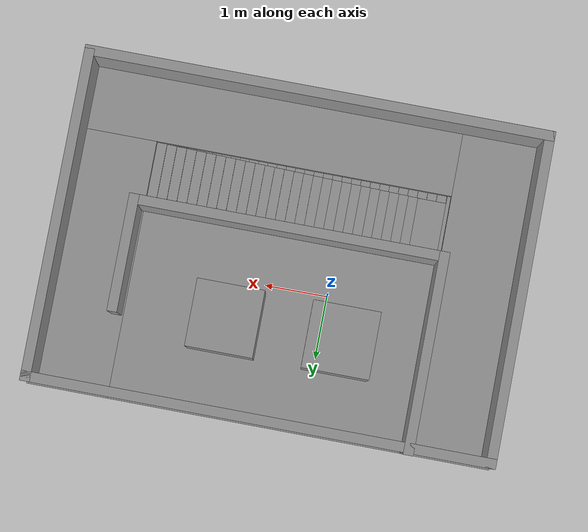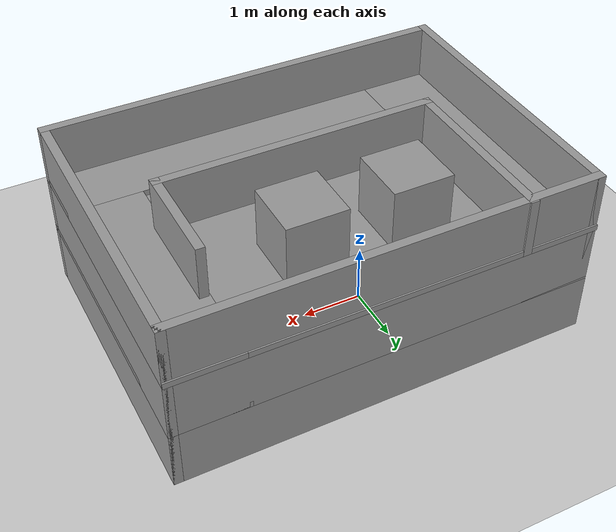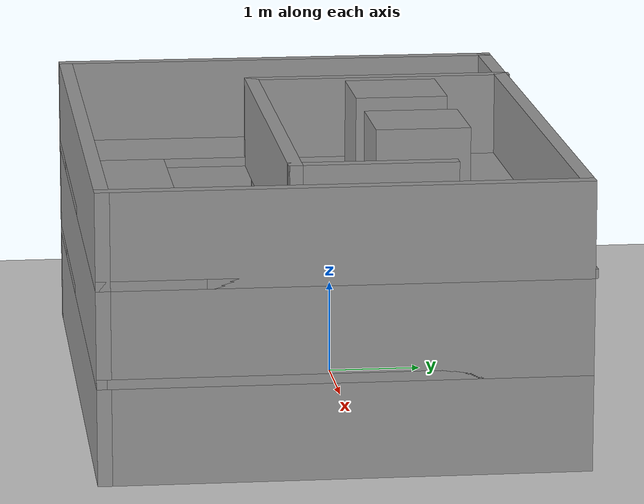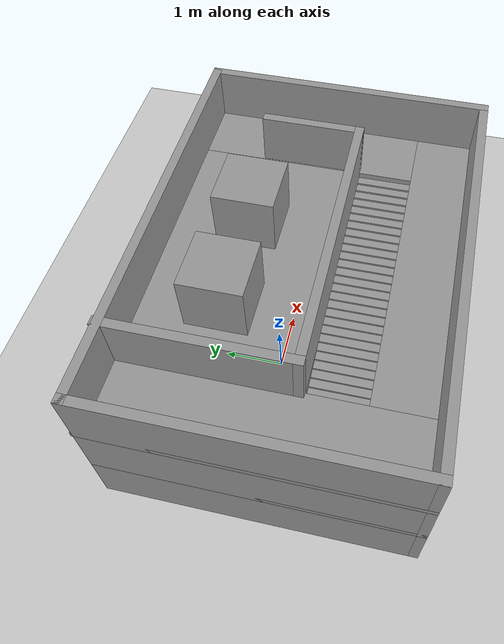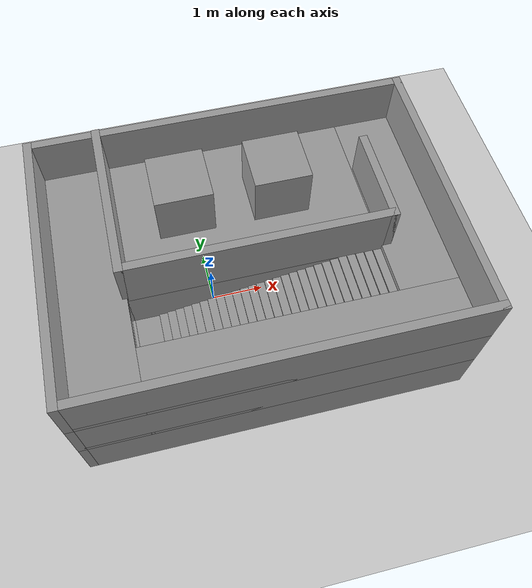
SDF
<sdf version="1.7">
 <world name="default">
  <light name="sun" type="directional">
   <pose>0 0 10 0 -0 0</pose>
   <diffuse>0.8 0.8 0.8 1</diffuse>
   <specular>0.2 0.2 0.2 1</specular>
   <attenuation>
    <range>1000</range>
    <constant>0.9</constant>
    <linear>0.01</linear>
    <quadratic>0.001</quadratic>
   </attenuation>
   <direction>-0.5 0.1 -0.9</direction>
   <spot><inner_angle>0</inner_angle><outer_angle>0</outer_angle><falloff>0</falloff></spot>
  </light>
  <model name="ground_plane">
   <static>1</static>
   <link name="link">
    <collision name="collision">
     <geometry><plane><normal>0 0 1</normal><size>100 100</size></plane></geometry>
     <surface>
      <contact><collide_bitmask>65535</collide_bitmask></contact>
      <friction><ode><mu>100</mu><mu2>50</mu2></ode></friction>
     </surface>
    </collision>
    <visual name="visual">
     <cast_shadows>0</cast_shadows>
     <geometry><plane><normal>0 0 1</normal><size>100 100</size></plane></geometry>
     <material>
      <script><uri>file://media/materials/scripts/gazebo.material</uri><name>Gazebo/Grey</name></script>
     </material>
    </visual>
   </link>
  </model>
  <gravity>0 0 -9.8</gravity>
  <magnetic_field>6e-06 2.3e-05 -4.2e-05</magnetic_field>
  <atmosphere type="adiabatic"/>
  <physics type="ode">
   <max_step_size>0.001</max_step_size>
   <real_time_factor>1</real_time_factor>
   <real_time_update_rate>1000</real_time_update_rate>
  </physics>
  <scene><ambient>0.4 0.4 0.4 1</ambient><background>0.7 0.7 0.7 1</background><shadows>1</shadows></scene>
  <spherical_coordinates>
   <surface_model>EARTH_WGS84</surface_model>
   <latitude_deg>0</latitude_deg>
   <longitude_deg>0</longitude_deg>
   <elevation>0</elevation>
   <heading_deg>0</heading_deg>
  </spherical_coordinates>
  <model name="3F_building">
   <pose>0.674929 -0.295159 0 0 -0 0</pose>
   <link name="Floor_14">
    <pose>0 -0.0135 1 0 -0 0</pose>
    <visual name="Floor_14_Visual_0">
     <pose>-2.88538 0 0.05 0 -0 0</pose>
     <geometry><box><size>1.22924 5 0.1</size></box></geometry>
     <material>
      <script><uri>file://media/materials/scripts/gazebo.material</uri><name>Gazebo/Grey</name></script>
      <ambient>1 1 1 1</ambient>
     </material>
     <meta><layer>1</layer></meta>
    </visual>
    <collision name="Floor_14_Collision_0">
     <geometry><box><size>1.22924 5 0.1</size></box></geometry>
     <pose>-2.88538 0 0.05 0 -0 0</pose>
    </collision>
    <visual name="Floor_14_Visual_1">
     <pose>-2.24272 -0.5568 0.05 0 -0 0</pose>
     <geometry><box><size>0.056072 3.8864 0.1</size></box></geometry>
     <material>
      <script><uri>file://media/materials/scripts/gazebo.material</uri><name>Gazebo/Grey</name></script>
      <ambient>1 1 1 1</ambient>
     </material>
     <meta><layer>1</layer></meta>
    </visual>
    <collision name="Floor_14_Collision_1">
     <geometry><box><size>0.056072 3.8864 0.1</size></box></geometry>
     <pose>-2.24272 -0.5568 0.05 0 -0 0</pose>
    </collision>
    <visual name="Floor_14_Visual_2">
     <pose>0.642656 -2.44643 0.05 0 -0 0</pose>
     <geometry><box><size>5.71469 0.107138 0.1</size></box></geometry>
     <material>
      <script><uri>file://media/materials/scripts/gazebo.material</uri><name>Gazebo/Grey</name></script>
      <ambient>1 1 1 1</ambient>
     </material>
     <meta><layer>1</layer></meta>
    </visual>
    <collision name="Floor_14_Collision_2">
     <geometry><box><size>5.71469 0.107138 0.1</size></box></geometry>
     <pose>0.642656 -2.44643 0.05 0 -0 0</pose>
    </collision>
    <visual name="Floor_14_Visual_3">
     <pose>2.89266 0.053569 0.05 0 -0 0</pose>
     <geometry><box><size>1.21469 4.89286 0.1</size></box></geometry>
     <material>
      <script><uri>file://media/materials/scripts/gazebo.material</uri><name>Gazebo/Grey</name></script>
      <ambient>1 1 1 1</ambient>
     </material>
     <meta><layer>1</layer></meta>
    </visual>
    <collision name="Floor_14_Collision_3">
     <geometry><box><size>1.21469 4.89286 0.1</size></box></geometry>
     <pose>2.89266 0.053569 0.05 0 -0 0</pose>
    </collision>
    <visual name="Floor_14_Visual_4">
     <pose>0.035312 -0.00323 0.05 0 -0 0</pose>
     <geometry><box><size>4.5 2.77926 0.1</size></box></geometry>
     <material>
      <script><uri>file://media/materials/scripts/gazebo.material</uri><name>Gazebo/Grey</name></script>
      <ambient>1 1 1 1</ambient>
     </material>
     <meta><layer>1</layer></meta>
    </visual>
    <collision name="Floor_14_Collision_4">
     <geometry><box><size>4.5 2.77926 0.1</size></box></geometry>
     <pose>0.035312 -0.00323 0.05 0 -0 0</pose>
    </collision>
    <visual name="Floor_14_Visual_5">
     <pose>2.25728 1.9432 0.05 0 -0 0</pose>
     <geometry><box><size>0.056072 1.1136 0.1</size></box></geometry>
     <material>
      <script><uri>file://media/materials/scripts/gazebo.material</uri><name>Gazebo/Grey</name></script>
      <ambient>1 1 1 1</ambient>
     </material>
     <meta><layer>1</layer></meta>
    </visual>
    <collision name="Floor_14_Collision_5">
     <geometry><box><size>0.056072 1.1136 0.1</size></box></geometry>
     <pose>2.25728 1.9432 0.05 0 -0 0</pose>
    </collision>
    <visual name="Floor_14_Visual_6">
     <pose>-2.24272 2.4432 0.05 0 -0 0</pose>
     <geometry><box><size>0.056072 0.113599 0.1</size></box></geometry>
     <material>
      <script><uri>file://media/materials/scripts/gazebo.material</uri><name>Gazebo/Grey</name></script>
      <ambient>1 1 1 1</ambient>
     </material>
     <meta><layer>1</layer></meta>
    </visual>
    <collision name="Floor_14_Collision_6">
     <geometry><box><size>0.056072 0.113599 0.1</size></box></geometry>
     <pose>-2.24272 2.4432 0.05 0 -0 0</pose>
    </collision>
   </link>
   <link name="Floor_16">
    <pose>0 0 2 0 -0 0</pose>
    <visual name="Floor_16_Visual_0">
     <pose>-2.8604 0 0.05 0 -0 0</pose>
     <geometry><box><size>1.27921 5.027 0.1</size></box></geometry>
     <material>
      <script><uri>file://media/materials/scripts/gazebo.material</uri><name>Gazebo/Grey</name></script>
      <ambient>1 1 1 1</ambient>
     </material>
     <meta><layer>2</layer></meta>
    </visual>
    <collision name="Floor_16_Collision_0">
     <geometry><box><size>1.27921 5.027 0.1</size></box></geometry>
     <pose>-2.8604 0 0.05 0 -0 0</pose>
    </collision>
    <visual name="Floor_16_Visual_1">
     <pose>0.639605 -1.96001 0.05 0 -0 0</pose>
     <geometry><box><size>5.72079 1.10698 0.1</size></box></geometry>
     <material>
      <script><uri>file://media/materials/scripts/gazebo.material</uri><name>Gazebo/Grey</name></script>
      <ambient>1 1 1 1</ambient>
     </material>
     <meta><layer>2</layer></meta>
    </visual>
    <collision name="Floor_16_Collision_1">
     <geometry><box><size>5.72079 1.10698 0.1</size></box></geometry>
     <pose>0.639605 -1.96001 0.05 0 -0 0</pose>
    </collision>
    <visual name="Floor_16_Visual_2">
     <pose>2.8896 0.55349 0.05 0 -0 0</pose>
     <geometry><box><size>1.22079 3.92002 0.1</size></box></geometry>
     <material>
      <script><uri>file://media/materials/scripts/gazebo.material</uri><name>Gazebo/Grey</name></script>
      <ambient>1 1 1 1</ambient>
     </material>
     <meta><layer>2</layer></meta>
    </visual>
    <collision name="Floor_16_Collision_2">
     <geometry><box><size>1.22079 3.92002 0.1</size></box></geometry>
     <pose>2.8896 0.55349 0.05 0 -0 0</pose>
    </collision>
    <visual name="Floor_16_Visual_3">
     <pose>0.029209 1.05349 0.05 0 -0 0</pose>
     <geometry><box><size>4.5 2.92002 0.1</size></box></geometry>
     <material>
      <script><uri>file://media/materials/scripts/gazebo.material</uri><name>Gazebo/Grey</name></script>
      <ambient>1 1 1 1</ambient>
     </material>
     <meta><layer>2</layer></meta>
    </visual>
    <collision name="Floor_16_Collision_3">
     <geometry><box><size>4.5 2.92002 0.1</size></box></geometry>
     <pose>0.029209 1.05349 0.05 0 -0 0</pose>
    </collision>
   </link>
   <link name="Stairs_5">
    <visual name="Stairs_5_Visual_0">
     <pose>-2.19576 1.8729 0.016667 0 -0 1.5708</pose>
     <geometry><box><size>1 0.15 0.033333</size></box></geometry>
     <material>
      <script><uri>file://media/materials/scripts/gazebo.material</uri><name>Gazebo/Grey</name></script>
      <ambient>1 1 1 1</ambient>
     </material>
     <meta><layer>0</layer></meta>
    </visual>
    <collision name="Stairs_5_Collision_0">
     <geometry><box><size>1 0.15 0.033333</size></box></geometry>
     <pose>-2.19576 1.8729 0.016667 0 -0 1.5708</pose>
    </collision>
    <visual name="Stairs_5_Visual_1">
     <pose>-2.04576 1.8729 0.05 0 -0 1.5708</pose>
     <geometry><box><size>1 0.15 0.033333</size></box></geometry>
     <material>
      <script><uri>file://media/materials/scripts/gazebo.material</uri><name>Gazebo/Grey</name></script>
      <ambient>1 1 1 1</ambient>
     </material>
     <meta><layer>0</layer></meta>
    </visual>
    <collision name="Stairs_5_Collision_1">
     <geometry><box><size>1 0.15 0.033333</size></box></geometry>
     <pose>-2.04576 1.8729 0.05 0 -0 1.5708</pose>
    </collision>
    <visual name="Stairs_5_Visual_2">
     <pose>-1.89576 1.8729 0.083333 0 -0 1.5708</pose>
     <geometry><box><size>1 0.15 0.033333</size></box></geometry>
     <material>
      <script><uri>file://media/materials/scripts/gazebo.material</uri><name>Gazebo/Grey</name></script>
      <ambient>1 1 1 1</ambient>
     </material>
     <meta><layer>0</layer></meta>
    </visual>
    <collision name="Stairs_5_Collision_2">
     <geometry><box><size>1 0.15 0.033333</size></box></geometry>
     <pose>-1.89576 1.8729 0.083333 0 -0 1.5708</pose>
    </collision>
    <visual name="Stairs_5_Visual_3">
     <pose>-1.74576 1.8729 0.116667 0 -0 1.5708</pose>
     <geometry><box><size>1 0.15 0.033333</size></box></geometry>
     <material>
      <script><uri>file://media/materials/scripts/gazebo.material</uri><name>Gazebo/Grey</name></script>
      <ambient>1 1 1 1</ambient>
     </material>
     <meta><layer>0</layer></meta>
    </visual>
    <collision name="Stairs_5_Collision_3">
     <geometry><box><size>1 0.15 0.033333</size></box></geometry>
     <pose>-1.74576 1.8729 0.116667 0 -0 1.5708</pose>
    </collision>
    <visual name="Stairs_5_Visual_4">
     <pose>-1.59576 1.8729 0.15 0 -0 1.5708</pose>
     <geometry><box><size>1 0.15 0.033333</size></box></geometry>
     <material>
      <script><uri>file://media/materials/scripts/gazebo.material</uri><name>Gazebo/Grey</name></script>
      <ambient>1 1 1 1</ambient>
     </material>
     <meta><layer>0</layer></meta>
    </visual>
    <collision name="Stairs_5_Collision_4">
     <geometry><box><size>1 0.15 0.033333</size></box></geometry>
     <pose>-1.59576 1.8729 0.15 0 -0 1.5708</pose>
    </collision>
    <visual name="Stairs_5_Visual_5">
     <pose>-1.44576 1.8729 0.183333 0 -0 1.5708</pose>
     <geometry><box><size>1 0.15 0.033333</size></box></geometry>
     <material>
      <script><uri>file://media/materials/scripts/gazebo.material</uri><name>Gazebo/Grey</name></script>
      <ambient>1 1 1 1</ambient>
     </material>
     <meta><layer>0</layer></meta>
    </visual>
    <collision name="Stairs_5_Collision_5">
     <geometry><box><size>1 0.15 0.033333</size></box></geometry>
     <pose>-1.44576 1.8729 0.183333 0 -0 1.5708</pose>
    </collision>
    <visual name="Stairs_5_Visual_6">
     <pose>-1.29576 1.8729 0.216667 0 -0 1.5708</pose>
     <geometry><box><size>1 0.15 0.033333</size></box></geometry>
     <material>
      <script><uri>file://media/materials/scripts/gazebo.material</uri><name>Gazebo/Grey</name></script>
      <ambient>1 1 1 1</ambient>
     </material>
     <meta><layer>0</layer></meta>
    </visual>
    <collision name="Stairs_5_Collision_6">
     <geometry><box><size>1 0.15 0.033333</size></box></geometry>
     <pose>-1.29576 1.8729 0.216667 0 -0 1.5708</pose>
    </collision>
    <visual name="Stairs_5_Visual_7">
     <pose>-1.14576 1.8729 0.25 0 -0 1.5708</pose>
     <geometry><box><size>1 0.15 0.033333</size></box></geometry>
     <material>
      <script><uri>file://media/materials/scripts/gazebo.material</uri><name>Gazebo/Grey</name></script>
      <ambient>1 1 1 1</ambient>
     </material>
     <meta><layer>0</layer></meta>
    </visual>
    <collision name="Stairs_5_Collision_7">
     <geometry><box><size>1 0.15 0.033333</size></box></geometry>
     <pose>-1.14576 1.8729 0.25 0 -0 1.5708</pose>
    </collision>
    <visual name="Stairs_5_Visual_8">
     <pose>-0.99576 1.8729 0.283333 0 -0 1.5708</pose>
     <geometry><box><size>1 0.15 0.033333</size></box></geometry>
     <material>
      <script><uri>file://media/materials/scripts/gazebo.material</uri><name>Gazebo/Grey</name></script>
      <ambient>1 1 1 1</ambient>
     </material>
     <meta><layer>0</layer></meta>
    </visual>
    <collision name="Stairs_5_Collision_8">
     <geometry><box><size>1 0.15 0.033333</size></box></geometry>
     <pose>-0.99576 1.8729 0.283333 0 -0 1.5708</pose>
    </collision>
    <visual name="Stairs_5_Visual_9">
     <pose>-0.84576 1.8729 0.316667 0 -0 1.5708</pose>
     <geometry><box><size>1 0.15 0.033333</size></box></geometry>
     <material>
      <script><uri>file://media/materials/scripts/gazebo.material</uri><name>Gazebo/Grey</name></script>
      <ambient>1 1 1 1</ambient>
     </material>
     <meta><layer>0</layer></meta>
    </visual>
    <collision name="Stairs_5_Collision_9">
     <geometry><box><size>1 0.15 0.033333</size></box></geometry>
     <pose>-0.84576 1.8729 0.316667 0 -0 1.5708</pose>
    </collision>
    <visual name="Stairs_5_Visual_10">
     <pose>-0.69576 1.8729 0.35 0 -0 1.5708</pose>
     <geometry><box><size>1 0.15 0.033333</size></box></geometry>
     <material>
      <script><uri>file://media/materials/scripts/gazebo.material</uri><name>Gazebo/Grey</name></script>
      <ambient>1 1 1 1</ambient>
     </material>
     <meta><layer>0</layer></meta>
    </visual>
    <collision name="Stairs_5_Collision_10">
     <geometry><box><size>1 0.15 0.033333</size></box></geometry>
     <pose>-0.69576 1.8729 0.35 0 -0 1.5708</pose>
    </collision>
    <visual name="Stairs_5_Visual_11">
     <pose>-0.54576 1.8729 0.383333 0 -0 1.5708</pose>
     <geometry><box><size>1 0.15 0.033333</size></box></geometry>
     <material>
      <script><uri>file://media/materials/scripts/gazebo.material</uri><name>Gazebo/Grey</name></script>
      <ambient>1 1 1 1</ambient>
     </material>
     <meta><layer>0</layer></meta>
    </visual>
    <collision name="Stairs_5_Collision_11">
     <geometry><box><size>1 0.15 0.033333</size></box></geometry>
     <pose>-0.54576 1.8729 0.383333 0 -0 1.5708</pose>
    </collision>
    <visual name="Stairs_5_Visual_12">
     <pose>-0.39576 1.8729 0.416667 0 -0 1.5708</pose>
     <geometry><box><size>1 0.15 0.033333</size></box></geometry>
     <material>
      <script><uri>file://media/materials/scripts/gazebo.material</uri><name>Gazebo/Grey</name></script>
      <ambient>1 1 1 1</ambient>
     </material>
     <meta><layer>0</layer></meta>
    </visual>
    <collision name="Stairs_5_Collision_12">
     <geometry><box><size>1 0.15 0.033333</size></box></geometry>
     <pose>-0.39576 1.8729 0.416667 0 -0 1.5708</pose>
    </collision>
    <visual name="Stairs_5_Visual_13">
     <pose>-0.24576 1.8729 0.45 0 -0 1.5708</pose>
     <geometry><box><size>1 0.15 0.033333</size></box></geometry>
     <material>
      <script><uri>file://media/materials/scripts/gazebo.material</uri><name>Gazebo/Grey</name></script>
      <ambient>1 1 1 1</ambient>
     </material>
     <meta><layer>0</layer></meta>
    </visual>
    <collision name="Stairs_5_Collision_13">
     <geometry><box><size>1 0.15 0.033333</size></box></geometry>
     <pose>-0.24576 1.8729 0.45 0 -0 1.5708</pose>
    </collision>
    <visual name="Stairs_5_Visual_14">
     <pose>-0.09576 1.8729 0.483333 0 -0 1.5708</pose>
     <geometry><box><size>1 0.15 0.033333</size></box></geometry>
     <material>
      <script><uri>file://media/materials/scripts/gazebo.material</uri><name>Gazebo/Grey</name></script>
      <ambient>1 1 1 1</ambient>
     </material>
     <meta><layer>0</layer></meta>
    </visual>
    <collision name="Stairs_5_Collision_14">
     <geometry><box><size>1 0.15 0.033333</size></box></geometry>
     <pose>-0.09576 1.8729 0.483333 0 -0 1.5708</pose>
    </collision>
    <visual name="Stairs_5_Visual_15">
     <pose>0.05424 1.8729 0.516667 0 -0 1.5708</pose>
     <geometry><box><size>1 0.15 0.033333</size></box></geometry>
     <material>
      <script><uri>file://media/materials/scripts/gazebo.material</uri><name>Gazebo/Grey</name></script>
      <ambient>1 1 1 1</ambient>
     </material>
     <meta><layer>0</layer></meta>
    </visual>
    <collision name="Stairs_5_Collision_15">
     <geometry><box><size>1 0.15 0.033333</size></box></geometry>
     <pose>0.05424 1.8729 0.516667 0 -0 1.5708</pose>
    </collision>
    <visual name="Stairs_5_Visual_16">
     <pose>0.20424 1.8729 0.55 0 -0 1.5708</pose>
     <geometry><box><size>1 0.15 0.033333</size></box></geometry>
     <material>
      <script><uri>file://media/materials/scripts/gazebo.material</uri><name>Gazebo/Grey</name></script>
      <ambient>1 1 1 1</ambient>
     </material>
     <meta><layer>0</layer></meta>
    </visual>
    <collision name="Stairs_5_Collision_16">
     <geometry><box><size>1 0.15 0.033333</size></box></geometry>
     <pose>0.20424 1.8729 0.55 0 -0 1.5708</pose>
    </collision>
    <visual name="Stairs_5_Visual_17">
     <pose>0.35424 1.8729 0.583333 0 -0 1.5708</pose>
     <geometry><box><size>1 0.15 0.033333</size></box></geometry>
     <material>
      <script><uri>file://media/materials/scripts/gazebo.material</uri><name>Gazebo/Grey</name></script>
      <ambient>1 1 1 1</ambient>
     </material>
     <meta><layer>0</layer></meta>
    </visual>
    <collision name="Stairs_5_Collision_17">
     <geometry><box><size>1 0.15 0.033333</size></box></geometry>
     <pose>0.35424 1.8729 0.583333 0 -0 1.5708</pose>
    </collision>
    <visual name="Stairs_5_Visual_18">
     <pose>0.50424 1.8729 0.616667 0 -0 1.5708</pose>
     <geometry><box><size>1 0.15 0.033333</size></box></geometry>
     <material>
      <script><uri>file://media/materials/scripts/gazebo.material</uri><name>Gazebo/Grey</name></script>
      <ambient>1 1 1 1</ambient>
     </material>
     <meta><layer>0</layer></meta>
    </visual>
    <collision name="Stairs_5_Collision_18">
     <geometry><box><size>1 0.15 0.033333</size></box></geometry>
     <pose>0.50424 1.8729 0.616667 0 -0 1.5708</pose>
    </collision>
    <visual name="Stairs_5_Visual_19">
     <pose>0.65424 1.8729 0.65 0 -0 1.5708</pose>
     <geometry><box><size>1 0.15 0.033333</size></box></geometry>
     <material>
      <script><uri>file://media/materials/scripts/gazebo.material</uri><name>Gazebo/Grey</name></script>
      <ambient>1 1 1 1</ambient>
     </material>
     <meta><layer>0</layer></meta>
    </visual>
    <collision name="Stairs_5_Collision_19">
     <geometry><box><size>1 0.15 0.033333</size></box></geometry>
     <pose>0.65424 1.8729 0.65 0 -0 1.5708</pose>
    </collision>
    <visual name="Stairs_5_Visual_20">
     <pose>0.80424 1.8729 0.683333 0 -0 1.5708</pose>
     <geometry><box><size>1 0.15 0.033333</size></box></geometry>
     <material>
      <script><uri>file://media/materials/scripts/gazebo.material</uri><name>Gazebo/Grey</name></script>
      <ambient>1 1 1 1</ambient>
     </material>
     <meta><layer>0</layer></meta>
    </visual>
    <collision name="Stairs_5_Collision_20">
     <geometry><box><size>1 0.15 0.033333</size></box></geometry>
     <pose>0.80424 1.8729 0.683333 0 -0 1.5708</pose>
    </collision>
    <visual name="Stairs_5_Visual_21">
     <pose>0.95424 1.8729 0.716667 0 -0 1.5708</pose>
     <geometry><box><size>1 0.15 0.033333</size></box></geometry>
     <material>
      <script><uri>file://media/materials/scripts/gazebo.material</uri><name>Gazebo/Grey</name></script>
      <ambient>1 1 1 1</ambient>
     </material>
     <meta><layer>0</layer></meta>
    </visual>
    <collision name="Stairs_5_Collision_21">
     <geometry><box><size>1 0.15 0.033333</size></box></geometry>
     <pose>0.95424 1.8729 0.716667 0 -0 1.5708</pose>
    </collision>
    <visual name="Stairs_5_Visual_22">
     <pose>1.10424 1.8729 0.75 0 -0 1.5708</pose>
     <geometry><box><size>1 0.15 0.033333</size></box></geometry>
     <material>
      <script><uri>file://media/materials/scripts/gazebo.material</uri><name>Gazebo/Grey</name></script>
      <ambient>1 1 1 1</ambient>
     </material>
     <meta><layer>0</layer></meta>
    </visual>
    <collision name="Stairs_5_Collision_22">
     <geometry><box><size>1 0.15 0.033333</size></box></geometry>
     <pose>1.10424 1.8729 0.75 0 -0 1.5708</pose>
    </collision>
    <visual name="Stairs_5_Visual_23">
     <pose>1.25424 1.8729 0.783333 0 -0 1.5708</pose>
     <geometry><box><size>1 0.15 0.033333</size></box></geometry>
     <material>
      <script><uri>file://media/materials/scripts/gazebo.material</uri><name>Gazebo/Grey</name></script>
      <ambient>1 1 1 1</ambient>
     </material>
     <meta><layer>0</layer></meta>
    </visual>
    <collision name="Stairs_5_Collision_23">
     <geometry><box><size>1 0.15 0.033333</size></box></geometry>
     <pose>1.25424 1.8729 0.783333 0 -0 1.5708</pose>
    </collision>
    <visual name="Stairs_5_Visual_24">
     <pose>1.40424 1.8729 0.816667 0 -0 1.5708</pose>
     <geometry><box><size>1 0.15 0.033333</size></box></geometry>
     <material>
      <script><uri>file://media/materials/scripts/gazebo.material</uri><name>Gazebo/Grey</name></script>
      <ambient>1 1 1 1</ambient>
     </material>
     <meta><layer>0</layer></meta>
    </visual>
    <collision name="Stairs_5_Collision_24">
     <geometry><box><size>1 0.15 0.033333</size></box></geometry>
     <pose>1.40424 1.8729 0.816667 0 -0 1.5708</pose>
    </collision>
    <visual name="Stairs_5_Visual_25">
     <pose>1.55424 1.8729 0.85 0 -0 1.5708</pose>
     <geometry><box><size>1 0.15 0.033333</size></box></geometry>
     <material>
      <script><uri>file://media/materials/scripts/gazebo.material</uri><name>Gazebo/Grey</name></script>
      <ambient>1 1 1 1</ambient>
     </material>
     <meta><layer>0</layer></meta>
    </visual>
    <collision name="Stairs_5_Collision_25">
     <geometry><box><size>1 0.15 0.033333</size></box></geometry>
     <pose>1.55424 1.8729 0.85 0 -0 1.5708</pose>
    </collision>
    <visual name="Stairs_5_Visual_26">
     <pose>1.70424 1.8729 0.883333 0 -0 1.5708</pose>
     <geometry><box><size>1 0.15 0.033333</size></box></geometry>
     <material>
      <script><uri>file://media/materials/scripts/gazebo.material</uri><name>Gazebo/Grey</name></script>
      <ambient>1 1 1 1</ambient>
     </material>
     <meta><layer>0</layer></meta>
    </visual>
    <collision name="Stairs_5_Collision_26">
     <geometry><box><size>1 0.15 0.033333</size></box></geometry>
     <pose>1.70424 1.8729 0.883333 0 -0 1.5708</pose>
    </collision>
    <visual name="Stairs_5_Visual_27">
     <pose>1.85424 1.8729 0.916667 0 -0 1.5708</pose>
     <geometry><box><size>1 0.15 0.033333</size></box></geometry>
     <material>
      <script><uri>file://media/materials/scripts/gazebo.material</uri><name>Gazebo/Grey</name></script>
      <ambient>1 1 1 1</ambient>
     </material>
     <meta><layer>0</layer></meta>
    </visual>
    <collision name="Stairs_5_Collision_27">
     <geometry><box><size>1 0.15 0.033333</size></box></geometry>
     <pose>1.85424 1.8729 0.916667 0 -0 1.5708</pose>
    </collision>
    <visual name="Stairs_5_Visual_28">
     <pose>2.00424 1.8729 0.95 0 -0 1.5708</pose>
     <geometry><box><size>1 0.15 0.033333</size></box></geometry>
     <material>
      <script><uri>file://media/materials/scripts/gazebo.material</uri><name>Gazebo/Grey</name></script>
      <ambient>1 1 1 1</ambient>
     </material>
     <meta><layer>0</layer></meta>
    </visual>
    <collision name="Stairs_5_Collision_28">
     <geometry><box><size>1 0.15 0.033333</size></box></geometry>
     <pose>2.00424 1.8729 0.95 0 -0 1.5708</pose>
    </collision>
    <visual name="Stairs_5_Visual_29">
     <pose>2.15424 1.8729 0.983333 0 -0 1.5708</pose>
     <geometry><box><size>1 0.15 0.033333</size></box></geometry>
     <material>
      <script><uri>file://media/materials/scripts/gazebo.material</uri><name>Gazebo/Grey</name></script>
      <ambient>1 1 1 1</ambient>
     </material>
     <meta><layer>0</layer></meta>
    </visual>
    <collision name="Stairs_5_Collision_29">
     <geometry><box><size>1 0.15 0.033333</size></box></geometry>
     <pose>2.15424 1.8729 0.983333 0 -0 1.5708</pose>
    </collision>
   </link>
   <link name="Stairs_7">
    <visual name="Stairs_7_Visual_0">
     <pose>2.21031 -1.90636 0.016667 0 -0 -1.5708</pose>
     <geometry><box><size>1 0.15 0.033333</size></box></geometry>
     <material>
      <script><uri>file://media/materials/scripts/gazebo.material</uri><name>Gazebo/Grey</name></script>
      <ambient>1 1 1 1</ambient>
     </material>
     <meta><layer>0</layer></meta>
    </visual>
    <collision name="Stairs_7_Collision_0">
     <geometry><box><size>1 0.15 0.033333</size></box></geometry>
     <pose>2.21031 -1.90636 0.016667 0 -0 -1.5708</pose>
    </collision>
    <visual name="Stairs_7_Visual_1">
     <pose>2.06031 -1.90636 0.05 0 -0 -1.5708</pose>
     <geometry><box><size>1 0.15 0.033333</size></box></geometry>
     <material>
      <script><uri>file://media/materials/scripts/gazebo.material</uri><name>Gazebo/Grey</name></script>
      <ambient>1 1 1 1</ambient>
     </material>
     <meta><layer>0</layer></meta>
    </visual>
    <collision name="Stairs_7_Collision_1">
     <geometry><box><size>1 0.15 0.033333</size></box></geometry>
     <pose>2.06031 -1.90636 0.05 0 -0 -1.5708</pose>
    </collision>
    <visual name="Stairs_7_Visual_2">
     <pose>1.91031 -1.90636 0.083333 0 -0 -1.5708</pose>
     <geometry><box><size>1 0.15 0.033333</size></box></geometry>
     <material>
      <script><uri>file://media/materials/scripts/gazebo.material</uri><name>Gazebo/Grey</name></script>
      <ambient>1 1 1 1</ambient>
     </material>
     <meta><layer>0</layer></meta>
    </visual>
    <collision name="Stairs_7_Collision_2">
     <geometry><box><size>1 0.15 0.033333</size></box></geometry>
     <pose>1.91031 -1.90636 0.083333 0 -0 -1.5708</pose>
    </collision>
    <visual name="Stairs_7_Visual_3">
     <pose>1.76031 -1.90636 0.116667 0 -0 -1.5708</pose>
     <geometry><box><size>1 0.15 0.033333</size></box></geometry>
     <material>
      <script><uri>file://media/materials/scripts/gazebo.material</uri><name>Gazebo/Grey</name></script>
      <ambient>1 1 1 1</ambient>
     </material>
     <meta><layer>0</layer></meta>
    </visual>
    <collision name="Stairs_7_Collision_3">
     <geometry><box><size>1 0.15 0.033333</size></box></geometry>
     <pose>1.76031 -1.90636 0.116667 0 -0 -1.5708</pose>
    </collision>
    <visual name="Stairs_7_Visual_4">
     <pose>1.61031 -1.90636 0.15 0 -0 -1.5708</pose>
     <geometry><box><size>1 0.15 0.033333</size></box></geometry>
     <material>
      <script><uri>file://media/materials/scripts/gazebo.material</uri><name>Gazebo/Grey</name></script>
      <ambient>1 1 1 1</ambient>
     </material>
     <meta><layer>0</layer></meta>
    </visual>
    <collision name="Stairs_7_Collision_4">
     <geometry><box><size>1 0.15 0.033333</size></box></geometry>
     <pose>1.61031 -1.90636 0.15 0 -0 -1.5708</pose>
    </collision>
    <visual name="Stairs_7_Visual_5">
     <pose>1.46031 -1.90636 0.183333 0 -0 -1.5708</pose>
     <geometry><box><size>1 0.15 0.033333</size></box></geometry>
     <material>
      <script><uri>file://media/materials/scripts/gazebo.material</uri><name>Gazebo/Grey</name></script>
      <ambient>1 1 1 1</ambient>
     </material>
     <meta><layer>0</layer></meta>
    </visual>
    <collision name="Stairs_7_Collision_5">
     <geometry><box><size>1 0.15 0.033333</size></box></geometry>
     <pose>1.46031 -1.90636 0.183333 0 -0 -1.5708</pose>
    </collision>
    <visual name="Stairs_7_Visual_6">
     <pose>1.31031 -1.90636 0.216667 0 -0 -1.5708</pose>
     <geometry><box><size>1 0.15 0.033333</size></box></geometry>
     <material>
      <script><uri>file://media/materials/scripts/gazebo.material</uri><name>Gazebo/Grey</name></script>
      <ambient>1 1 1 1</ambient>
     </material>
     <meta><layer>0</layer></meta>
    </visual>
    <collision name="Stairs_7_Collision_6">
     <geometry><box><size>1 0.15 0.033333</size></box></geometry>
     <pose>1.31031 -1.90636 0.216667 0 -0 -1.5708</pose>
    </collision>
    <visual name="Stairs_7_Visual_7">
     <pose>1.16031 -1.90636 0.25 0 -0 -1.5708</pose>
     <geometry><box><size>1 0.15 0.033333</size></box></geometry>
     <material>
      <script><uri>file://media/materials/scripts/gazebo.material</uri><name>Gazebo/Grey</name></script>
      <ambient>1 1 1 1</ambient>
     </material>
     <meta><layer>0</layer></meta>
    </visual>
    <collision name="Stairs_7_Collision_7">
     <geometry><box><size>1 0.15 0.033333</size></box></geometry>
     <pose>1.16031 -1.90636 0.25 0 -0 -1.5708</pose>
    </collision>
    <visual name="Stairs_7_Visual_8">
     <pose>1.01031 -1.90636 0.283333 0 -0 -1.5708</pose>
     <geometry><box><size>1 0.15 0.033333</size></box></geometry>
     <material>
      <script><uri>file://media/materials/scripts/gazebo.material</uri><name>Gazebo/Grey</name></script>
      <ambient>1 1 1 1</ambient>
     </material>
     <meta><layer>0</layer></meta>
    </visual>
    <collision name="Stairs_7_Collision_8">
     <geometry><box><size>1 0.15 0.033333</size></box></geometry>
     <pose>1.01031 -1.90636 0.283333 0 -0 -1.5708</pose>
    </collision>
    <visual name="Stairs_7_Visual_9">
     <pose>0.860312 -1.90636 0.316667 0 -0 -1.5708</pose>
     <geometry><box><size>1 0.15 0.033333</size></box></geometry>
     <material>
      <script><uri>file://media/materials/scripts/gazebo.material</uri><name>Gazebo/Grey</name></script>
      <ambient>1 1 1 1</ambient>
     </material>
     <meta><layer>0</layer></meta>
    </visual>
    <collision name="Stairs_7_Collision_9">
     <geometry><box><size>1 0.15 0.033333</size></box></geometry>
     <pose>0.860312 -1.90636 0.316667 0 -0 -1.5708</pose>
    </collision>
    <visual name="Stairs_7_Visual_10">
     <pose>0.710312 -1.90636 0.35 0 -0 -1.5708</pose>
     <geometry><box><size>1 0.15 0.033333</size></box></geometry>
     <material>
      <script><uri>file://media/materials/scripts/gazebo.material</uri><name>Gazebo/Grey</name></script>
      <ambient>1 1 1 1</ambient>
     </material>
     <meta><layer>0</layer></meta>
    </visual>
    <collision name="Stairs_7_Collision_10">
     <geometry><box><size>1 0.15 0.033333</size></box></geometry>
     <pose>0.710312 -1.90636 0.35 0 -0 -1.5708</pose>
    </collision>
    <visual name="Stairs_7_Visual_11">
     <pose>0.560312 -1.90636 0.383333 0 -0 -1.5708</pose>
     <geometry><box><size>1 0.15 0.033333</size></box></geometry>
     <material>
      <script><uri>file://media/materials/scripts/gazebo.material</uri><name>Gazebo/Grey</name></script>
      <ambient>1 1 1 1</ambient>
     </material>
     <meta><layer>0</layer></meta>
    </visual>
    <collision name="Stairs_7_Collision_11">
     <geometry><box><size>1 0.15 0.033333</size></box></geometry>
     <pose>0.560312 -1.90636 0.383333 0 -0 -1.5708</pose>
    </collision>
    <visual name="Stairs_7_Visual_12">
     <pose>0.410312 -1.90636 0.416667 0 -0 -1.5708</pose>
     <geometry><box><size>1 0.15 0.033333</size></box></geometry>
     <material>
      <script><uri>file://media/materials/scripts/gazebo.material</uri><name>Gazebo/Grey</name></script>
      <ambient>1 1 1 1</ambient>
     </material>
     <meta><layer>0</layer></meta>
    </visual>
    <collision name="Stairs_7_Collision_12">
     <geometry><box><size>1 0.15 0.033333</size></box></geometry>
     <pose>0.410312 -1.90636 0.416667 0 -0 -1.5708</pose>
    </collision>
    <visual name="Stairs_7_Visual_13">
     <pose>0.260312 -1.90636 0.45 0 -0 -1.5708</pose>
     <geometry><box><size>1 0.15 0.033333</size></box></geometry>
     <material>
      <script><uri>file://media/materials/scripts/gazebo.material</uri><name>Gazebo/Grey</name></script>
      <ambient>1 1 1 1</ambient>
     </material>
     <meta><layer>0</layer></meta>
    </visual>
    <collision name="Stairs_7_Collision_13">
     <geometry><box><size>1 0.15 0.033333</size></box></geometry>
     <pose>0.260312 -1.90636 0.45 0 -0 -1.5708</pose>
    </collision>
    <visual name="Stairs_7_Visual_14">
     <pose>0.110312 -1.90636 0.483333 0 -0 -1.5708</pose>
     <geometry><box><size>1 0.15 0.033333</size></box></geometry>
     <material>
      <script><uri>file://media/materials/scripts/gazebo.material</uri><name>Gazebo/Grey</name></script>
      <ambient>1 1 1 1</ambient>
     </material>
     <meta><layer>0</layer></meta>
    </visual>
    <collision name="Stairs_7_Collision_14">
     <geometry><box><size>1 0.15 0.033333</size></box></geometry>
     <pose>0.110312 -1.90636 0.483333 0 -0 -1.5708</pose>
    </collision>
    <visual name="Stairs_7_Visual_15">
     <pose>-0.039688 -1.90636 0.516667 0 -0 -1.5708</pose>
     <geometry><box><size>1 0.15 0.033333</size></box></geometry>
     <material>
      <script><uri>file://media/materials/scripts/gazebo.material</uri><name>Gazebo/Grey</name></script>
      <ambient>1 1 1 1</ambient>
     </material>
     <meta><layer>0</layer></meta>
    </visual>
    <collision name="Stairs_7_Collision_15">
     <geometry><box><size>1 0.15 0.033333</size></box></geometry>
     <pose>-0.039688 -1.90636 0.516667 0 -0 -1.5708</pose>
    </collision>
    <visual name="Stairs_7_Visual_16">
     <pose>-0.189688 -1.90636 0.55 0 -0 -1.5708</pose>
     <geometry><box><size>1 0.15 0.033333</size></box></geometry>
     <material>
      <script><uri>file://media/materials/scripts/gazebo.material</uri><name>Gazebo/Grey</name></script>
      <ambient>1 1 1 1</ambient>
     </material>
     <meta><layer>0</layer></meta>
    </visual>
    <collision name="Stairs_7_Collision_16">
     <geometry><box><size>1 0.15 0.033333</size></box></geometry>
     <pose>-0.189688 -1.90636 0.55 0 -0 -1.5708</pose>
    </collision>
    <visual name="Stairs_7_Visual_17">
     <pose>-0.339688 -1.90636 0.583333 0 -0 -1.5708</pose>
     <geometry><box><size>1 0.15 0.033333</size></box></geometry>
     <material>
      <script><uri>file://media/materials/scripts/gazebo.material</uri><name>Gazebo/Grey</name></script>
      <ambient>1 1 1 1</ambient>
     </material>
     <meta><layer>0</layer></meta>
    </visual>
    <collision name="Stairs_7_Collision_17">
     <geometry><box><size>1 0.15 0.033333</size></box></geometry>
     <pose>-0.339688 -1.90636 0.583333 0 -0 -1.5708</pose>
    </collision>
    <visual name="Stairs_7_Visual_18">
     <pose>-0.489688 -1.90636 0.616667 0 -0 -1.5708</pose>
     <geometry><box><size>1 0.15 0.033333</size></box></geometry>
     <material>
      <script><uri>file://media/materials/scripts/gazebo.material</uri><name>Gazebo/Grey</name></script>
      <ambient>1 1 1 1</ambient>
     </material>
     <meta><layer>0</layer></meta>
    </visual>
    <collision name="Stairs_7_Collision_18">
     <geometry><box><size>1 0.15 0.033333</size></box></geometry>
     <pose>-0.489688 -1.90636 0.616667 0 -0 -1.5708</pose>
    </collision>
    <visual name="Stairs_7_Visual_19">
     <pose>-0.639688 -1.90636 0.65 0 -0 -1.5708</pose>
     <geometry><box><size>1 0.15 0.033333</size></box></geometry>
     <material>
      <script><uri>file://media/materials/scripts/gazebo.material</uri><name>Gazebo/Grey</name></script>
      <ambient>1 1 1 1</ambient>
     </material>
     <meta><layer>0</layer></meta>
    </visual>
    <collision name="Stairs_7_Collision_19">
     <geometry><box><size>1 0.15 0.033333</size></box></geometry>
     <pose>-0.639688 -1.90636 0.65 0 -0 -1.5708</pose>
    </collision>
    <visual name="Stairs_7_Visual_20">
     <pose>-0.789688 -1.90636 0.683333 0 -0 -1.5708</pose>
     <geometry><box><size>1 0.15 0.033333</size></box></geometry>
     <material>
      <script><uri>file://media/materials/scripts/gazebo.material</uri><name>Gazebo/Grey</name></script>
      <ambient>1 1 1 1</ambient>
     </material>
     <meta><layer>0</layer></meta>
    </visual>
    <collision name="Stairs_7_Collision_20">
     <geometry><box><size>1 0.15 0.033333</size></box></geometry>
     <pose>-0.789688 -1.90636 0.683333 0 -0 -1.5708</pose>
    </collision>
    <visual name="Stairs_7_Visual_21">
     <pose>-0.939688 -1.90636 0.716667 0 -0 -1.5708</pose>
     <geometry><box><size>1 0.15 0.033333</size></box></geometry>
     <material>
      <script><uri>file://media/materials/scripts/gazebo.material</uri><name>Gazebo/Grey</name></script>
      <ambient>1 1 1 1</ambient>
     </material>
     <meta><layer>0</layer></meta>
    </visual>
    <collision name="Stairs_7_Collision_21">
     <geometry><box><size>1 0.15 0.033333</size></box></geometry>
     <pose>-0.939688 -1.90636 0.716667 0 -0 -1.5708</pose>
    </collision>
    <visual name="Stairs_7_Visual_22">
     <pose>-1.08969 -1.90636 0.75 0 -0 -1.5708</pose>
     <geometry><box><size>1 0.15 0.033333</size></box></geometry>
     <material>
      <script><uri>file://media/materials/scripts/gazebo.material</uri><name>Gazebo/Grey</name></script>
      <ambient>1 1 1 1</ambient>
     </material>
     <meta><layer>0</layer></meta>
    </visual>
    <collision name="Stairs_7_Collision_22">
     <geometry><box><size>1 0.15 0.033333</size></box></geometry>
     <pose>-1.08969 -1.90636 0.75 0 -0 -1.5708</pose>
    </collision>
    <visual name="Stairs_7_Visual_23">
     <pose>-1.23969 -1.90636 0.783333 0 -0 -1.5708</pose>
     <geometry><box><size>1 0.15 0.033333</size></box></geometry>
     <material>
      <script><uri>file://media/materials/scripts/gazebo.material</uri><name>Gazebo/Grey</name></script>
      <ambient>1 1 1 1</ambient>
     </material>
     <meta><layer>0</layer></meta>
    </visual>
    <collision name="Stairs_7_Collision_23">
     <geometry><box><size>1 0.15 0.033333</size></box></geometry>
     <pose>-1.23969 -1.90636 0.783333 0 -0 -1.5708</pose>
    </collision>
    <visual name="Stairs_7_Visual_24">
     <pose>-1.38969 -1.90636 0.816667 0 -0 -1.5708</pose>
     <geometry><box><size>1 0.15 0.033333</size></box></geometry>
     <material>
      <script><uri>file://media/materials/scripts/gazebo.material</uri><name>Gazebo/Grey</name></script>
      <ambient>1 1 1 1</ambient>
     </material>
     <meta><layer>0</layer></meta>
    </visual>
    <collision name="Stairs_7_Collision_24">
     <geometry><box><size>1 0.15 0.033333</size></box></geometry>
     <pose>-1.38969 -1.90636 0.816667 0 -0 -1.5708</pose>
    </collision>
    <visual name="Stairs_7_Visual_25">
     <pose>-1.53969 -1.90636 0.85 0 -0 -1.5708</pose>
     <geometry><box><size>1 0.15 0.033333</size></box></geometry>
     <material>
      <script><uri>file://media/materials/scripts/gazebo.material</uri><name>Gazebo/Grey</name></script>
      <ambient>1 1 1 1</ambient>
     </material>
     <meta><layer>0</layer></meta>
    </visual>
    <collision name="Stairs_7_Collision_25">
     <geometry><box><size>1 0.15 0.033333</size></box></geometry>
     <pose>-1.53969 -1.90636 0.85 0 -0 -1.5708</pose>
    </collision>
    <visual name="Stairs_7_Visual_26">
     <pose>-1.68969 -1.90636 0.883333 0 -0 -1.5708</pose>
     <geometry><box><size>1 0.15 0.033333</size></box></geometry>
     <material>
      <script><uri>file://media/materials/scripts/gazebo.material</uri><name>Gazebo/Grey</name></script>
      <ambient>1 1 1 1</ambient>
     </material>
     <meta><layer>0</layer></meta>
    </visual>
    <collision name="Stairs_7_Collision_26">
     <geometry><box><size>1 0.15 0.033333</size></box></geometry>
     <pose>-1.68969 -1.90636 0.883333 0 -0 -1.5708</pose>
    </collision>
    <visual name="Stairs_7_Visual_27">
     <pose>-1.83969 -1.90636 0.916667 0 -0 -1.5708</pose>
     <geometry><box><size>1 0.15 0.033333</size></box></geometry>
     <material>
      <script><uri>file://media/materials/scripts/gazebo.material</uri><name>Gazebo/Grey</name></script>
      <ambient>1 1 1 1</ambient>
     </material>
     <meta><layer>0</layer></meta>
    </visual>
    <collision name="Stairs_7_Collision_27">
     <geometry><box><size>1 0.15 0.033333</size></box></geometry>
     <pose>-1.83969 -1.90636 0.916667 0 -0 -1.5708</pose>
    </collision>
    <visual name="Stairs_7_Visual_28">
     <pose>-1.98969 -1.90636 0.95 0 -0 -1.5708</pose>
     <geometry><box><size>1 0.15 0.033333</size></box></geometry>
     <material>
      <script><uri>file://media/materials/scripts/gazebo.material</uri><name>Gazebo/Grey</name></script>
      <ambient>1 1 1 1</ambient>
     </material>
     <meta><layer>0</layer></meta>
    </visual>
    <collision name="Stairs_7_Collision_28">
     <geometry><box><size>1 0.15 0.033333</size></box></geometry>
     <pose>-1.98969 -1.90636 0.95 0 -0 -1.5708</pose>
    </collision>
    <visual name="Stairs_7_Visual_29">
     <pose>-2.13969 -1.90636 0.983333 0 -0 -1.5708</pose>
     <geometry><box><size>1 0.15 0.033333</size></box></geometry>
     <material>
      <script><uri>file://media/materials/scripts/gazebo.material</uri><name>Gazebo/Grey</name></script>
      <ambient>1 1 1 1</ambient>
     </material>
     <meta><layer>0</layer></meta>
    </visual>
    <collision name="Stairs_7_Collision_29">
     <geometry><box><size>1 0.15 0.033333</size></box></geometry>
     <pose>-2.13969 -1.90636 0.983333 0 -0 -1.5708</pose>
    </collision>
   </link>
   <link name="Stairs_9">
    <visual name="Stairs_9_Visual_0">
     <pose>-2.14579 -0.906519 1.01667 0 -0 1.5708</pose>
     <geometry><box><size>1 0.15 0.033333</size></box></geometry>
     <material>
      <script><uri>file://media/materials/scripts/gazebo.material</uri><name>Gazebo/Grey</name></script>
      <ambient>1 1 1 1</ambient>
     </material>
     <meta><layer>1</layer></meta>
    </visual>
    <collision name="Stairs_9_Collision_0">
     <geometry><box><size>1 0.15 0.033333</size></box></geometry>
     <pose>-2.14579 -0.906519 1.01667 0 -0 1.5708</pose>
    </collision>
    <visual name="Stairs_9_Visual_1">
     <pose>-1.99579 -0.906519 1.05 0 -0 1.5708</pose>
     <geometry><box><size>1 0.15 0.033333</size></box></geometry>
     <material>
      <script><uri>file://media/materials/scripts/gazebo.material</uri><name>Gazebo/Grey</name></script>
      <ambient>1 1 1 1</ambient>
     </material>
     <meta><layer>1</layer></meta>
    </visual>
    <collision name="Stairs_9_Collision_1">
     <geometry><box><size>1 0.15 0.033333</size></box></geometry>
     <pose>-1.99579 -0.906519 1.05 0 -0 1.5708</pose>
    </collision>
    <visual name="Stairs_9_Visual_2">
     <pose>-1.84579 -0.906519 1.08333 0 -0 1.5708</pose>
     <geometry><box><size>1 0.15 0.033333</size></box></geometry>
     <material>
      <script><uri>file://media/materials/scripts/gazebo.material</uri><name>Gazebo/Grey</name></script>
      <ambient>1 1 1 1</ambient>
     </material>
     <meta><layer>1</layer></meta>
    </visual>
    <collision name="Stairs_9_Collision_2">
     <geometry><box><size>1 0.15 0.033333</size></box></geometry>
     <pose>-1.84579 -0.906519 1.08333 0 -0 1.5708</pose>
    </collision>
    <visual name="Stairs_9_Visual_3">
     <pose>-1.69579 -0.906519 1.11667 0 -0 1.5708</pose>
     <geometry><box><size>1 0.15 0.033333</size></box></geometry>
     <material>
      <script><uri>file://media/materials/scripts/gazebo.material</uri><name>Gazebo/Grey</name></script>
      <ambient>1 1 1 1</ambient>
     </material>
     <meta><layer>1</layer></meta>
    </visual>
    <collision name="Stairs_9_Collision_3">
     <geometry><box><size>1 0.15 0.033333</size></box></geometry>
     <pose>-1.69579 -0.906519 1.11667 0 -0 1.5708</pose>
    </collision>
    <visual name="Stairs_9_Visual_4">
     <pose>-1.54579 -0.906519 1.15 0 -0 1.5708</pose>
     <geometry><box><size>1 0.15 0.033333</size></box></geometry>
     <material>
      <script><uri>file://media/materials/scripts/gazebo.material</uri><name>Gazebo/Grey</name></script>
      <ambient>1 1 1 1</ambient>
     </material>
     <meta><layer>1</layer></meta>
    </visual>
    <collision name="Stairs_9_Collision_4">
     <geometry><box><size>1 0.15 0.033333</size></box></geometry>
     <pose>-1.54579 -0.906519 1.15 0 -0 1.5708</pose>
    </collision>
    <visual name="Stairs_9_Visual_5">
     <pose>-1.39579 -0.906519 1.18333 0 -0 1.5708</pose>
     <geometry><box><size>1 0.15 0.033333</size></box></geometry>
     <material>
      <script><uri>file://media/materials/scripts/gazebo.material</uri><name>Gazebo/Grey</name></script>
      <ambient>1 1 1 1</ambient>
     </material>
     <meta><layer>1</layer></meta>
    </visual>
    <collision name="Stairs_9_Collision_5">
     <geometry><box><size>1 0.15 0.033333</size></box></geometry>
     <pose>-1.39579 -0.906519 1.18333 0 -0 1.5708</pose>
    </collision>
    <visual name="Stairs_9_Visual_6">
     <pose>-1.24579 -0.906519 1.21667 0 -0 1.5708</pose>
     <geometry><box><size>1 0.15 0.033333</size></box></geometry>
     <material>
      <script><uri>file://media/materials/scripts/gazebo.material</uri><name>Gazebo/Grey</name></script>
      <ambient>1 1 1 1</ambient>
     </material>
     <meta><layer>1</layer></meta>
    </visual>
    <collision name="Stairs_9_Collision_6">
     <geometry><box><size>1 0.15 0.033333</size></box></geometry>
     <pose>-1.24579 -0.906519 1.21667 0 -0 1.5708</pose>
    </collision>
    <visual name="Stairs_9_Visual_7">
     <pose>-1.09579 -0.906519 1.25 0 -0 1.5708</pose>
     <geometry><box><size>1 0.15 0.033333</size></box></geometry>
     <material>
      <script><uri>file://media/materials/scripts/gazebo.material</uri><name>Gazebo/Grey</name></script>
      <ambient>1 1 1 1</ambient>
     </material>
     <meta><layer>1</layer></meta>
    </visual>
    <collision name="Stairs_9_Collision_7">
     <geometry><box><size>1 0.15 0.033333</size></box></geometry>
     <pose>-1.09579 -0.906519 1.25 0 -0 1.5708</pose>
    </collision>
    <visual name="Stairs_9_Visual_8">
     <pose>-0.945791 -0.906519 1.28333 0 -0 1.5708</pose>
     <geometry><box><size>1 0.15 0.033333</size></box></geometry>
     <material>
      <script><uri>file://media/materials/scripts/gazebo.material</uri><name>Gazebo/Grey</name></script>
      <ambient>1 1 1 1</ambient>
     </material>
     <meta><layer>1</layer></meta>
    </visual>
    <collision name="Stairs_9_Collision_8">
     <geometry><box><size>1 0.15 0.033333</size></box></geometry>
     <pose>-0.945791 -0.906519 1.28333 0 -0 1.5708</pose>
    </collision>
    <visual name="Stairs_9_Visual_9">
     <pose>-0.795791 -0.906519 1.31667 0 -0 1.5708</pose>
     <geometry><box><size>1 0.15 0.033333</size></box></geometry>
     <material>
      <script><uri>file://media/materials/scripts/gazebo.material</uri><name>Gazebo/Grey</name></script>
      <ambient>1 1 1 1</ambient>
     </material>
     <meta><layer>1</layer></meta>
    </visual>
    <collision name="Stairs_9_Collision_9">
     <geometry><box><size>1 0.15 0.033333</size></box></geometry>
     <pose>-0.795791 -0.906519 1.31667 0 -0 1.5708</pose>
    </collision>
    <visual name="Stairs_9_Visual_10">
     <pose>-0.645791 -0.906519 1.35 0 -0 1.5708</pose>
     <geometry><box><size>1 0.15 0.033333</size></box></geometry>
     <material>
      <script><uri>file://media/materials/scripts/gazebo.material</uri><name>Gazebo/Grey</name></script>
      <ambient>1 1 1 1</ambient>
     </material>
     <meta><layer>1</layer></meta>
    </visual>
    <collision name="Stairs_9_Collision_10">
     <geometry><box><size>1 0.15 0.033333</size></box></geometry>
     <pose>-0.645791 -0.906519 1.35 0 -0 1.5708</pose>
    </collision>
    <visual name="Stairs_9_Visual_11">
     <pose>-0.495791 -0.906519 1.38333 0 -0 1.5708</pose>
     <geometry><box><size>1 0.15 0.033333</size></box></geometry>
     <material>
      <script><uri>file://media/materials/scripts/gazebo.material</uri><name>Gazebo/Grey</name></script>
      <ambient>1 1 1 1</ambient>
     </material>
     <meta><layer>1</layer></meta>
    </visual>
    <collision name="Stairs_9_Collision_11">
     <geometry><box><size>1 0.15 0.033333</size></box></geometry>
     <pose>-0.495791 -0.906519 1.38333 0 -0 1.5708</pose>
    </collision>
    <visual name="Stairs_9_Visual_12">
     <pose>-0.345791 -0.906519 1.41667 0 -0 1.5708</pose>
     <geometry><box><size>1 0.15 0.033333</size></box></geometry>
     <material>
      <script><uri>file://media/materials/scripts/gazebo.material</uri><name>Gazebo/Grey</name></script>
      <ambient>1 1 1 1</ambient>
     </material>
     <meta><layer>1</layer></meta>
    </visual>
    <collision name="Stairs_9_Collision_12">
     <geometry><box><size>1 0.15 0.033333</size></box></geometry>
     <pose>-0.345791 -0.906519 1.41667 0 -0 1.5708</pose>
    </collision>
    <visual name="Stairs_9_Visual_13">
     <pose>-0.195791 -0.906519 1.45 0 -0 1.5708</pose>
     <geometry><box><size>1 0.15 0.033333</size></box></geometry>
     <material>
      <script><uri>file://media/materials/scripts/gazebo.material</uri><name>Gazebo/Grey</name></script>
      <ambient>1 1 1 1</ambient>
     </material>
     <meta><layer>1</layer></meta>
    </visual>
    <collision name="Stairs_9_Collision_13">
     <geometry><box><size>1 0.15 0.033333</size></box></geometry>
     <pose>-0.195791 -0.906519 1.45 0 -0 1.5708</pose>
    </collision>
    <visual name="Stairs_9_Visual_14">
     <pose>-0.045791 -0.906519 1.48333 0 -0 1.5708</pose>
     <geometry><box><size>1 0.15 0.033333</size></box></geometry>
     <material>
      <script><uri>file://media/materials/scripts/gazebo.material</uri><name>Gazebo/Grey</name></script>
      <ambient>1 1 1 1</ambient>
     </material>
     <meta><layer>1</layer></meta>
    </visual>
    <collision name="Stairs_9_Collision_14">
     <geometry><box><size>1 0.15 0.033333</size></box></geometry>
     <pose>-0.045791 -0.906519 1.48333 0 -0 1.5708</pose>
    </collision>
    <visual name="Stairs_9_Visual_15">
     <pose>0.104209 -0.906519 1.51667 0 -0 1.5708</pose>
     <geometry><box><size>1 0.15 0.033333</size></box></geometry>
     <material>
      <script><uri>file://media/materials/scripts/gazebo.material</uri><name>Gazebo/Grey</name></script>
      <ambient>1 1 1 1</ambient>
     </material>
     <meta><layer>1</layer></meta>
    </visual>
    <collision name="Stairs_9_Collision_15">
     <geometry><box><size>1 0.15 0.033333</size></box></geometry>
     <pose>0.104209 -0.906519 1.51667 0 -0 1.5708</pose>
    </collision>
    <visual name="Stairs_9_Visual_16">
     <pose>0.254209 -0.906519 1.55 0 -0 1.5708</pose>
     <geometry><box><size>1 0.15 0.033333</size></box></geometry>
     <material>
      <script><uri>file://media/materials/scripts/gazebo.material</uri><name>Gazebo/Grey</name></script>
      <ambient>1 1 1 1</ambient>
     </material>
     <meta><layer>1</layer></meta>
    </visual>
    <collision name="Stairs_9_Collision_16">
     <geometry><box><size>1 0.15 0.033333</size></box></geometry>
     <pose>0.254209 -0.906519 1.55 0 -0 1.5708</pose>
    </collision>
    <visual name="Stairs_9_Visual_17">
     <pose>0.404209 -0.906519 1.58333 0 -0 1.5708</pose>
     <geometry><box><size>1 0.15 0.033333</size></box></geometry>
     <material>
      <script><uri>file://media/materials/scripts/gazebo.material</uri><name>Gazebo/Grey</name></script>
      <ambient>1 1 1 1</ambient>
     </material>
     <meta><layer>1</layer></meta>
    </visual>
    <collision name="Stairs_9_Collision_17">
     <geometry><box><size>1 0.15 0.033333</size></box></geometry>
     <pose>0.404209 -0.906519 1.58333 0 -0 1.5708</pose>
    </collision>
    <visual name="Stairs_9_Visual_18">
     <pose>0.554209 -0.906519 1.61667 0 -0 1.5708</pose>
     <geometry><box><size>1 0.15 0.033333</size></box></geometry>
     <material>
      <script><uri>file://media/materials/scripts/gazebo.material</uri><name>Gazebo/Grey</name></script>
      <ambient>1 1 1 1</ambient>
     </material>
     <meta><layer>1</layer></meta>
    </visual>
    <collision name="Stairs_9_Collision_18">
     <geometry><box><size>1 0.15 0.033333</size></box></geometry>
     <pose>0.554209 -0.906519 1.61667 0 -0 1.5708</pose>
    </collision>
    <visual name="Stairs_9_Visual_19">
     <pose>0.704209 -0.906519 1.65 0 -0 1.5708</pose>
     <geometry><box><size>1 0.15 0.033333</size></box></geometry>
     <material>
      <script><uri>file://media/materials/scripts/gazebo.material</uri><name>Gazebo/Grey</name></script>
      <ambient>1 1 1 1</ambient>
     </material>
     <meta><layer>1</layer></meta>
    </visual>
    <collision name="Stairs_9_Collision_19">
     <geometry><box><size>1 0.15 0.033333</size></box></geometry>
     <pose>0.704209 -0.906519 1.65 0 -0 1.5708</pose>
    </collision>
    <visual name="Stairs_9_Visual_20">
     <pose>0.854209 -0.906519 1.68333 0 -0 1.5708</pose>
     <geometry><box><size>1 0.15 0.033333</size></box></geometry>
     <material>
      <script><uri>file://media/materials/scripts/gazebo.material</uri><name>Gazebo/Grey</name></script>
      <ambient>1 1 1 1</ambient>
     </material>
     <meta><layer>1</layer></meta>
    </visual>
    <collision name="Stairs_9_Collision_20">
     <geometry><box><size>1 0.15 0.033333</size></box></geometry>
     <pose>0.854209 -0.906519 1.68333 0 -0 1.5708</pose>
    </collision>
    <visual name="Stairs_9_Visual_21">
     <pose>1.00421 -0.906519 1.71667 0 -0 1.5708</pose>
     <geometry><box><size>1 0.15 0.033333</size></box></geometry>
     <material>
      <script><uri>file://media/materials/scripts/gazebo.material</uri><name>Gazebo/Grey</name></script>
      <ambient>1 1 1 1</ambient>
     </material>
     <meta><layer>1</layer></meta>
    </visual>
    <collision name="Stairs_9_Collision_21">
     <geometry><box><size>1 0.15 0.033333</size></box></geometry>
     <pose>1.00421 -0.906519 1.71667 0 -0 1.5708</pose>
    </collision>
    <visual name="Stairs_9_Visual_22">
     <pose>1.15421 -0.906519 1.75 0 -0 1.5708</pose>
     <geometry><box><size>1 0.15 0.033333</size></box></geometry>
     <material>
      <script><uri>file://media/materials/scripts/gazebo.material</uri><name>Gazebo/Grey</name></script>
      <ambient>1 1 1 1</ambient>
     </material>
     <meta><layer>1</layer></meta>
    </visual>
    <collision name="Stairs_9_Collision_22">
     <geometry><box><size>1 0.15 0.033333</size></box></geometry>
     <pose>1.15421 -0.906519 1.75 0 -0 1.5708</pose>
    </collision>
    <visual name="Stairs_9_Visual_23">
     <pose>1.30421 -0.906519 1.78333 0 -0 1.5708</pose>
     <geometry><box><size>1 0.15 0.033333</size></box></geometry>
     <material>
      <script><uri>file://media/materials/scripts/gazebo.material</uri><name>Gazebo/Grey</name></script>
      <ambient>1 1 1 1</ambient>
     </material>
     <meta><layer>1</layer></meta>
    </visual>
    <collision name="Stairs_9_Collision_23">
     <geometry><box><size>1 0.15 0.033333</size></box></geometry>
     <pose>1.30421 -0.906519 1.78333 0 -0 1.5708</pose>
    </collision>
    <visual name="Stairs_9_Visual_24">
     <pose>1.45421 -0.906519 1.81667 0 -0 1.5708</pose>
     <geometry><box><size>1 0.15 0.033333</size></box></geometry>
     <material>
      <script><uri>file://media/materials/scripts/gazebo.material</uri><name>Gazebo/Grey</name></script>
      <ambient>1 1 1 1</ambient>
     </material>
     <meta><layer>1</layer></meta>
    </visual>
    <collision name="Stairs_9_Collision_24">
     <geometry><box><size>1 0.15 0.033333</size></box></geometry>
     <pose>1.45421 -0.906519 1.81667 0 -0 1.5708</pose>
    </collision>
    <visual name="Stairs_9_Visual_25">
     <pose>1.60421 -0.906519 1.85 0 -0 1.5708</pose>
     <geometry><box><size>1 0.15 0.033333</size></box></geometry>
     <material>
      <script><uri>file://media/materials/scripts/gazebo.material</uri><name>Gazebo/Grey</name></script>
      <ambient>1 1 1 1</ambient>
     </material>
     <meta><layer>1</layer></meta>
    </visual>
    <collision name="Stairs_9_Collision_25">
     <geometry><box><size>1 0.15 0.033333</size></box></geometry>
     <pose>1.60421 -0.906519 1.85 0 -0 1.5708</pose>
    </collision>
    <visual name="Stairs_9_Visual_26">
     <pose>1.75421 -0.906519 1.88333 0 -0 1.5708</pose>
     <geometry><box><size>1 0.15 0.033333</size></box></geometry>
     <material>
      <script><uri>file://media/materials/scripts/gazebo.material</uri><name>Gazebo/Grey</name></script>
      <ambient>1 1 1 1</ambient>
     </material>
     <meta><layer>1</layer></meta>
    </visual>
    <collision name="Stairs_9_Collision_26">
     <geometry><box><size>1 0.15 0.033333</size></box></geometry>
     <pose>1.75421 -0.906519 1.88333 0 -0 1.5708</pose>
    </collision>
    <visual name="Stairs_9_Visual_27">
     <pose>1.90421 -0.906519 1.91667 0 -0 1.5708</pose>
     <geometry><box><size>1 0.15 0.033333</size></box></geometry>
     <material>
      <script><uri>file://media/materials/scripts/gazebo.material</uri><name>Gazebo/Grey</name></script>
      <ambient>1 1 1 1</ambient>
     </material>
     <meta><layer>1</layer></meta>
    </visual>
    <collision name="Stairs_9_Collision_27">
     <geometry><box><size>1 0.15 0.033333</size></box></geometry>
     <pose>1.90421 -0.906519 1.91667 0 -0 1.5708</pose>
    </collision>
    <visual name="Stairs_9_Visual_28">
     <pose>2.05421 -0.906519 1.95 0 -0 1.5708</pose>
     <geometry><box><size>1 0.15 0.033333</size></box></geometry>
     <material>
      <script><uri>file://media/materials/scripts/gazebo.material</uri><name>Gazebo/Grey</name></script>
      <ambient>1 1 1 1</ambient>
     </material>
     <meta><layer>1</layer></meta>
    </visual>
    <collision name="Stairs_9_Collision_28">
     <geometry><box><size>1 0.15 0.033333</size></box></geometry>
     <pose>2.05421 -0.906519 1.95 0 -0 1.5708</pose>
    </collision>
    <visual name="Stairs_9_Visual_29">
     <pose>2.20421 -0.906519 1.98333 0 -0 1.5708</pose>
     <geometry><box><size>1 0.15 0.033333</size></box></geometry>
     <material>
      <script><uri>file://media/materials/scripts/gazebo.material</uri><name>Gazebo/Grey</name></script>
      <ambient>1 1 1 1</ambient>
     </material>
     <meta><layer>1</layer></meta>
    </visual>
    <collision name="Stairs_9_Collision_29">
     <geometry><box><size>1 0.15 0.033333</size></box></geometry>
     <pose>2.20421 -0.906519 1.98333 0 -0 1.5708</pose>
    </collision>
   </link>
   <link name="Wall_103">
    <collision name="Wall_103_Collision">
     <geometry><box><size>3 0.15 1</size></box></geometry>
     <pose>0 0 0.5 0 -0 0</pose>
    </collision>
    <visual name="Wall_103_Visual">
     <pose>0 0 0.5 0 -0 0</pose>
     <geometry><box><size>3 0.15 1</size></box></geometry>
     <material>
      <script><uri>file://media/materials/scripts/gazebo.material</uri><name>Gazebo/Grey</name></script>
      <ambient>1 1 1 1</ambient>
     </material>
     <meta><layer>2</layer></meta>
    </visual>
    <pose>-2.224 1.0135 2 0 -0 1.5708</pose>
   </link>
   <link name="Wall_106">
    <collision name="Wall_106_Collision">
     <geometry><box><size>1.75 0.15 1</size></box></geometry>
     <pose>0 0 0.5 0 -0 0</pose>
    </collision>
    <visual name="Wall_106_Visual">
     <pose>0 0 0.5 0 -0 0</pose>
     <geometry><box><size>1.75 0.15 1</size></box></geometry>
     <material>
      <script><uri>file://media/materials/scripts/gazebo.material</uri><name>Gazebo/Grey</name></script>
      <ambient>1 1 1 1</ambient>
     </material>
     <meta><layer>2</layer></meta>
    </visual>
    <pose>2.376 0.3885 2 0 -0 1.5708</pose>
   </link>
   <link name="Wall_14">
    <collision name="Wall_14_Collision">
     <geometry><box><size>5 0.15 1</size></box></geometry>
     <pose>0 0 0.5 0 -0 0</pose>
    </collision>
    <visual name="Wall_14_Visual">
     <pose>0 0 0.5 0 -0 0</pose>
     <geometry><box><size>5 0.15 1</size></box></geometry>
     <material>
      <script><uri>file://media/materials/scripts/gazebo.material</uri><name>Gazebo/Grey</name></script>
      <ambient>1 1 1 1</ambient>
     </material>
     <meta><layer>0</layer></meta>
    </visual>
    <pose>-3.425 -0.0135 0 0 -0 1.5708</pose>
   </link>
   <link name="Wall_18">
    <collision name="Wall_18_Collision">
     <geometry><box><size>7 0.15 1</size></box></geometry>
     <pose>0 0 0.5 0 -0 0</pose>
    </collision>
    <visual name="Wall_18_Visual">
     <pose>0 0 0.5 0 -0 0</pose>
     <geometry><box><size>7 0.15 1</size></box></geometry>
     <material>
      <script><uri>file://media/materials/scripts/gazebo.material</uri><name>Gazebo/Grey</name></script>
      <ambient>1 1 1 1</ambient>
     </material>
     <meta><layer>0</layer></meta>
    </visual>
    <pose>0 2.4115 0 0 -0 0</pose>
   </link>
   <link name="Wall_19">
    <collision name="Wall_19_Collision">
     <geometry><box><size>5 0.15 1</size></box></geometry>
     <pose>0 0 0.5 0 -0 0</pose>
    </collision>
    <visual name="Wall_19_Visual">
     <pose>0 0 0.5 0 -0 0</pose>
     <geometry><box><size>5 0.15 1</size></box></geometry>
     <material>
      <script><uri>file://media/materials/scripts/gazebo.material</uri><name>Gazebo/Grey</name></script>
      <ambient>1 1 1 1</ambient>
     </material>
     <meta><layer>0</layer></meta>
    </visual>
    <pose>3.425 -0.0135 0 0 -0 -1.5708</pose>
   </link>
   <link name="Wall_20">
    <collision name="Wall_20_Collision">
     <geometry><box><size>7 0.15 1</size></box></geometry>
     <pose>0 0 0.5 0 -0 0</pose>
    </collision>
    <visual name="Wall_20_Visual">
     <pose>0 0 0.5 0 -0 0</pose>
     <geometry><box><size>7 0.15 1</size></box></geometry>
     <material>
      <script><uri>file://media/materials/scripts/gazebo.material</uri><name>Gazebo/Grey</name></script>
      <ambient>1 1 1 1</ambient>
     </material>
     <meta><layer>0</layer></meta>
    </visual>
    <pose>0 -2.4385 0 0 -0 3.14159</pose>
   </link>
   <link name="Wall_42">
    <collision name="Wall_42_Collision">
     <geometry><box><size>5.75 0.15 1</size></box></geometry>
     <pose>0 0 0.5 0 -0 0</pose>
    </collision>
    <visual name="Wall_42_Visual">
     <pose>0 0 0.5 0 -0 0</pose>
     <geometry><box><size>5.75 0.15 1</size></box></geometry>
     <material>
      <script><uri>file://media/materials/scripts/gazebo.material</uri><name>Gazebo/Grey</name></script>
      <ambient>1 1 1 1</ambient>
     </material>
     <meta><layer>0</layer></meta>
    </visual>
    <pose>0.595 1.3205 0 0 -0 0</pose>
   </link>
   <link name="Wall_44">
    <collision name="Wall_44_Collision">
     <geometry><box><size>5.75 0.15 1</size></box></geometry>
     <pose>0 0 0.5 0 -0 0</pose>
    </collision>
    <visual name="Wall_44_Visual">
     <pose>0 0 0.5 0 -0 0</pose>
     <geometry><box><size>5.75 0.15 1</size></box></geometry>
     <material>
      <script><uri>file://media/materials/scripts/gazebo.material</uri><name>Gazebo/Grey</name></script>
      <ambient>1 1 1 1</ambient>
     </material>
     <meta><layer>0</layer></meta>
    </visual>
    <pose>-0.582 -1.3275 0 0 -0 0</pose>
   </link>
   <link name="Wall_46">
    <collision name="Wall_46_Collision">
     <geometry><box><size>1.794 0.15 1</size></box></geometry>
     <pose>0 0 0.5 0 -0 0</pose>
    </collision>
    <visual name="Wall_46_Visual">
     <pose>0 0 0.5 0 -0 0</pose>
     <geometry><box><size>1.794 0.15 1</size></box></geometry>
     <material>
      <script><uri>file://media/materials/scripts/gazebo.material</uri><name>Gazebo/Grey</name></script>
      <ambient>1 1 1 1</ambient>
     </material>
     <meta><layer>0</layer></meta>
    </visual>
    <pose>-1.636 0.4395 0 0 -0 -1.5708</pose>
   </link>
   <link name="Wall_47">
    <collision name="Wall_47_Collision">
     <geometry><box><size>2 0.15 1</size></box></geometry>
     <pose>0 0 0.5 0 -0 0</pose>
    </collision>
    <visual name="Wall_47_Visual">
     <pose>0 0 0.5 0 -0 0</pose>
     <geometry><box><size>2 0.15 1</size></box></geometry>
     <material>
      <script><uri>file://media/materials/scripts/gazebo.material</uri><name>Gazebo/Grey</name></script>
      <ambient>1 1 1 1</ambient>
     </material>
     <meta><layer>0</layer></meta>
    </visual>
    <pose>-0.711 -0.3825 0 0 -0 0</pose>
   </link>
   <link name="Wall_48">
    <collision name="Wall_48_Collision">
     <geometry><box><size>1.04373 0.15 1</size></box></geometry>
     <pose>0 0 0.5 0 -0 0</pose>
    </collision>
    <visual name="Wall_48_Visual">
     <pose>0 0 0.5 0 -0 0</pose>
     <geometry><box><size>1.04373 0.15 1</size></box></geometry>
     <material>
      <script><uri>file://media/materials/scripts/gazebo.material</uri><name>Gazebo/Grey</name></script>
      <ambient>1 1 1 1</ambient>
     </material>
     <meta><layer>0</layer></meta>
    </visual>
    <pose>0.214 0.0645 0 0 -0 1.5708</pose>
   </link>
   <link name="Wall_72">
    <collision name="Wall_72_Collision">
     <geometry><box><size>5 0.15 1</size></box></geometry>
     <pose>0 0 0.5 0 -0 0</pose>
    </collision>
    <visual name="Wall_72_Visual">
     <pose>0 0 0.5 0 -0 0</pose>
     <geometry><box><size>5 0.15 1</size></box></geometry>
     <material>
      <script><uri>file://media/materials/scripts/gazebo.material</uri><name>Gazebo/Grey</name></script>
      <ambient>1 1 1 1</ambient>
     </material>
     <meta><layer>1</layer></meta>
    </visual>
    <pose>-3.425 -0.0135 1 0 -0 1.5708</pose>
   </link>
   <link name="Wall_73">
    <collision name="Wall_73_Collision">
     <geometry><box><size>7 0.15 1</size></box></geometry>
     <pose>0 0 0.5 0 -0 0</pose>
    </collision>
    <visual name="Wall_73_Visual">
     <pose>0 0 0.5 0 -0 0</pose>
     <geometry><box><size>7 0.15 1</size></box></geometry>
     <material>
      <script><uri>file://media/materials/scripts/gazebo.material</uri><name>Gazebo/Grey</name></script>
      <ambient>1 1 1 1</ambient>
     </material>
     <meta><layer>1</layer></meta>
    </visual>
    <pose>0 2.4115 1 0 -0 0</pose>
   </link>
   <link name="Wall_74">
    <collision name="Wall_74_Collision">
     <geometry><box><size>5 0.15 1</size></box></geometry>
     <pose>0 0 0.5 0 -0 0</pose>
    </collision>
    <visual name="Wall_74_Visual">
     <pose>0 0 0.5 0 -0 0</pose>
     <geometry><box><size>5 0.15 1</size></box></geometry>
     <material>
      <script><uri>file://media/materials/scripts/gazebo.material</uri><name>Gazebo/Grey</name></script>
      <ambient>1 1 1 1</ambient>
     </material>
     <meta><layer>1</layer></meta>
    </visual>
    <pose>3.425 -0.0135 1 0 -0 -1.5708</pose>
   </link>
   <link name="Wall_75">
    <collision name="Wall_75_Collision">
     <geometry><box><size>7 0.15 1</size></box></geometry>
     <pose>0 0 0.5 0 -0 0</pose>
    </collision>
    <visual name="Wall_75_Visual">
     <pose>0 0 0.5 0 -0 0</pose>
     <geometry><box><size>7 0.15 1</size></box></geometry>
     <material>
      <script><uri>file://media/materials/scripts/gazebo.material</uri><name>Gazebo/Grey</name></script>
      <ambient>1 1 1 1</ambient>
     </material>
     <meta><layer>1</layer></meta>
    </visual>
    <pose>0 -2.4385 1 0 -0 3.14159</pose>
   </link>
   <link name="Wall_88">
    <collision name="Wall_88_Collision">
     <geometry><box><size>5.75 0.15 1</size></box></geometry>
     <pose>0 0 0.5 0 -0 0</pose>
    </collision>
    <visual name="Wall_88_Visual">
     <pose>0 0 0.5 0 -0 0</pose>
     <geometry><box><size>5.75 0.15 1</size></box></geometry>
     <material>
      <script><uri>file://media/materials/scripts/gazebo.material</uri><name>Gazebo/Grey</name></script>
      <ambient>1 1 1 1</ambient>
     </material>
     <meta><layer>1</layer></meta>
    </visual>
    <pose>0.589 -0.3345 1 0 -0 0</pose>
   </link>
   <link name="Wall_90">
    <collision name="Wall_90_Collision">
     <geometry><box><size>0.75 0.15 1</size></box></geometry>
     <pose>0 0 0.5 0 -0 0</pose>
    </collision>
    <visual name="Wall_90_Visual">
     <pose>0 0 0.5 0 -0 0</pose>
     <geometry><box><size>0.75 0.15 1</size></box></geometry>
     <material>
      <script><uri>file://media/materials/scripts/gazebo.material</uri><name>Gazebo/Grey</name></script>
      <ambient>1 1 1 1</ambient>
     </material>
     <meta><layer>1</layer></meta>
    </visual>
    <pose>-2.211 -0.0345 1 0 -0 1.5708</pose>
   </link>
   <link name="Wall_92">
    <collision name="Wall_92_Collision">
     <geometry><box><size>5 0.15 1</size></box></geometry>
     <pose>0 0 0.5 0 -0 0</pose>
    </collision>
    <visual name="Wall_92_Visual">
     <pose>0 0 0.5 0 -0 0</pose>
     <geometry><box><size>5 0.15 1</size></box></geometry>
     <material>
      <script><uri>file://media/materials/scripts/gazebo.material</uri><name>Gazebo/Grey</name></script>
      <ambient>1 1 1 1</ambient>
     </material>
     <meta><layer>2</layer></meta>
    </visual>
    <pose>-3.425 -0.0135 2 0 -0 1.5708</pose>
   </link>
   <link name="Wall_93">
    <collision name="Wall_93_Collision">
     <geometry><box><size>7 0.15 1</size></box></geometry>
     <pose>0 0 0.5 0 -0 0</pose>
    </collision>
    <visual name="Wall_93_Visual">
     <pose>0 0 0.5 0 -0 0</pose>
     <geometry><box><size>7 0.15 1</size></box></geometry>
     <material>
      <script><uri>file://media/materials/scripts/gazebo.material</uri><name>Gazebo/Grey</name></script>
      <ambient>1 1 1 1</ambient>
     </material>
     <meta><layer>2</layer></meta>
    </visual>
    <pose>0 2.4115 2 0 -0 0</pose>
   </link>
   <link name="Wall_94">
    <collision name="Wall_94_Collision">
     <geometry><box><size>5 0.15 1</size></box></geometry>
     <pose>0 0 0.5 0 -0 0</pose>
    </collision>
    <visual name="Wall_94_Visual">
     <pose>0 0 0.5 0 -0 0</pose>
     <geometry><box><size>5 0.15 1</size></box></geometry>
     <material>
      <script><uri>file://media/materials/scripts/gazebo.material</uri><name>Gazebo/Grey</name></script>
      <ambient>1 1 1 1</ambient>
     </material>
     <meta><layer>2</layer></meta>
    </visual>
    <pose>3.425 -0.0135 2 0 -0 -1.5708</pose>
   </link>
   <link name="Wall_95">
    <collision name="Wall_95_Collision">
     <geometry><box><size>7 0.15 1</size></box></geometry>
     <pose>0 0 0.5 0 -0 0</pose>
    </collision>
    <visual name="Wall_95_Visual">
     <pose>0 0 0.5 0 -0 0</pose>
     <geometry><box><size>7 0.15 1</size></box></geometry>
     <material>
      <script><uri>file://media/materials/scripts/gazebo.material</uri><name>Gazebo/Grey</name></script>
      <ambient>1 1 1 1</ambient>
     </material>
     <meta><layer>2</layer></meta>
    </visual>
    <pose>0 -2.4385 2 0 -0 3.14159</pose>
   </link>
   <link name="Wall_98">
    <collision name="Wall_98_Collision">
     <geometry><box><size>4.75 0.15 1</size></box></geometry>
     <pose>0 0 0.5 0 -0 0</pose>
    </collision>
    <visual name="Wall_98_Visual">
     <pose>0 0 0.5 0 -0 0</pose>
     <geometry><box><size>4.75 0.15 1</size></box></geometry>
     <material>
      <script><uri>file://media/materials/scripts/gazebo.material</uri><name>Gazebo/Grey</name></script>
      <ambient>1 1 1 1</ambient>
     </material>
     <meta><layer>2</layer></meta>
    </visual>
    <pose>0.076 -0.4115 2 0 -0 0</pose>
   </link>
   <static>1</static>
  </model>
  <model name="unit_box">
   <pose>1.41624 0.763613 2.6 -0 -0 -1e-06</pose>
   <link name="link">
    <inertial>
     <mass>1</mass>
     <inertia>
      <ixx>0.166667</ixx>
      <ixy>0</ixy>
      <ixz>0</ixz>
      <iyy>0.166667</iyy>
      <iyz>0</iyz>
      <izz>0.166667</izz>
     </inertia>
    </inertial>
    <collision name="collision"><geometry><box><size>1 1 1</size></box></geometry></collision>
    <visual name="visual">
     <geometry><box><size>1 1 1</size></box></geometry>
     <material>
      <script><name>Gazebo/Grey</name><uri>file://media/materials/scripts/gazebo.material</uri></script>
     </material>
    </visual>
   </link>
  </model>
  <model name="unit_box_clone">
   <pose>-0.29525 0.762458 2.6 -0 -0 -0</pose>
   <link name="link">
    <inertial>
     <mass>1</mass>
     <inertia>
      <ixx>0.166667</ixx>
      <ixy>0</ixy>
      <ixz>0</ixz>
      <iyy>0.166667</iyy>
      <iyz>0</iyz>
      <izz>0.166667</izz>
     </inertia>
    </inertial>
    <collision name="collision"><geometry><box><size>1 1 1</size></box></geometry></collision>
    <visual name="visual">
     <geometry><box><size>1 1 1</size></box></geometry>
     <material>
      <script><name>Gazebo/Grey</name><uri>file://media/materials/scripts/gazebo.material</uri></script>
     </material>
    </visual>
   </link>
  </model>
 </world>
</sdf>
